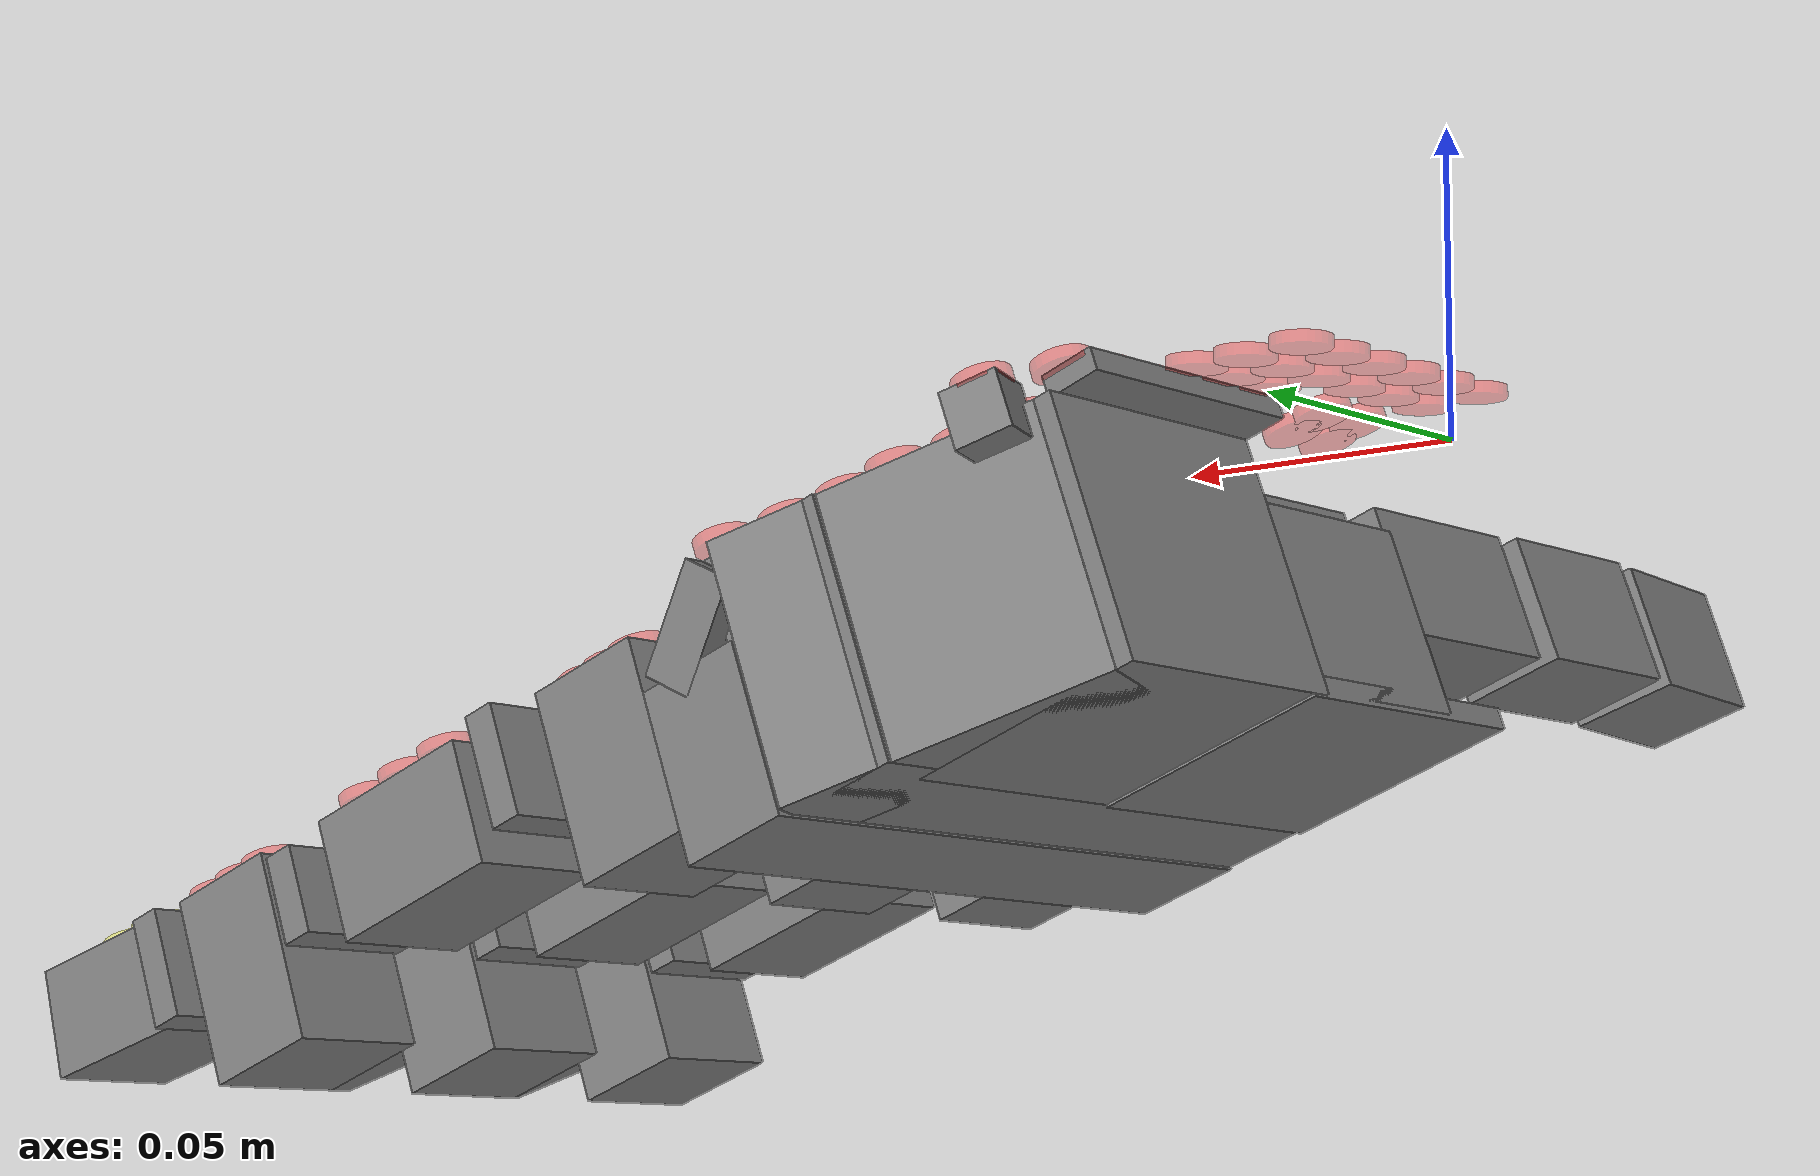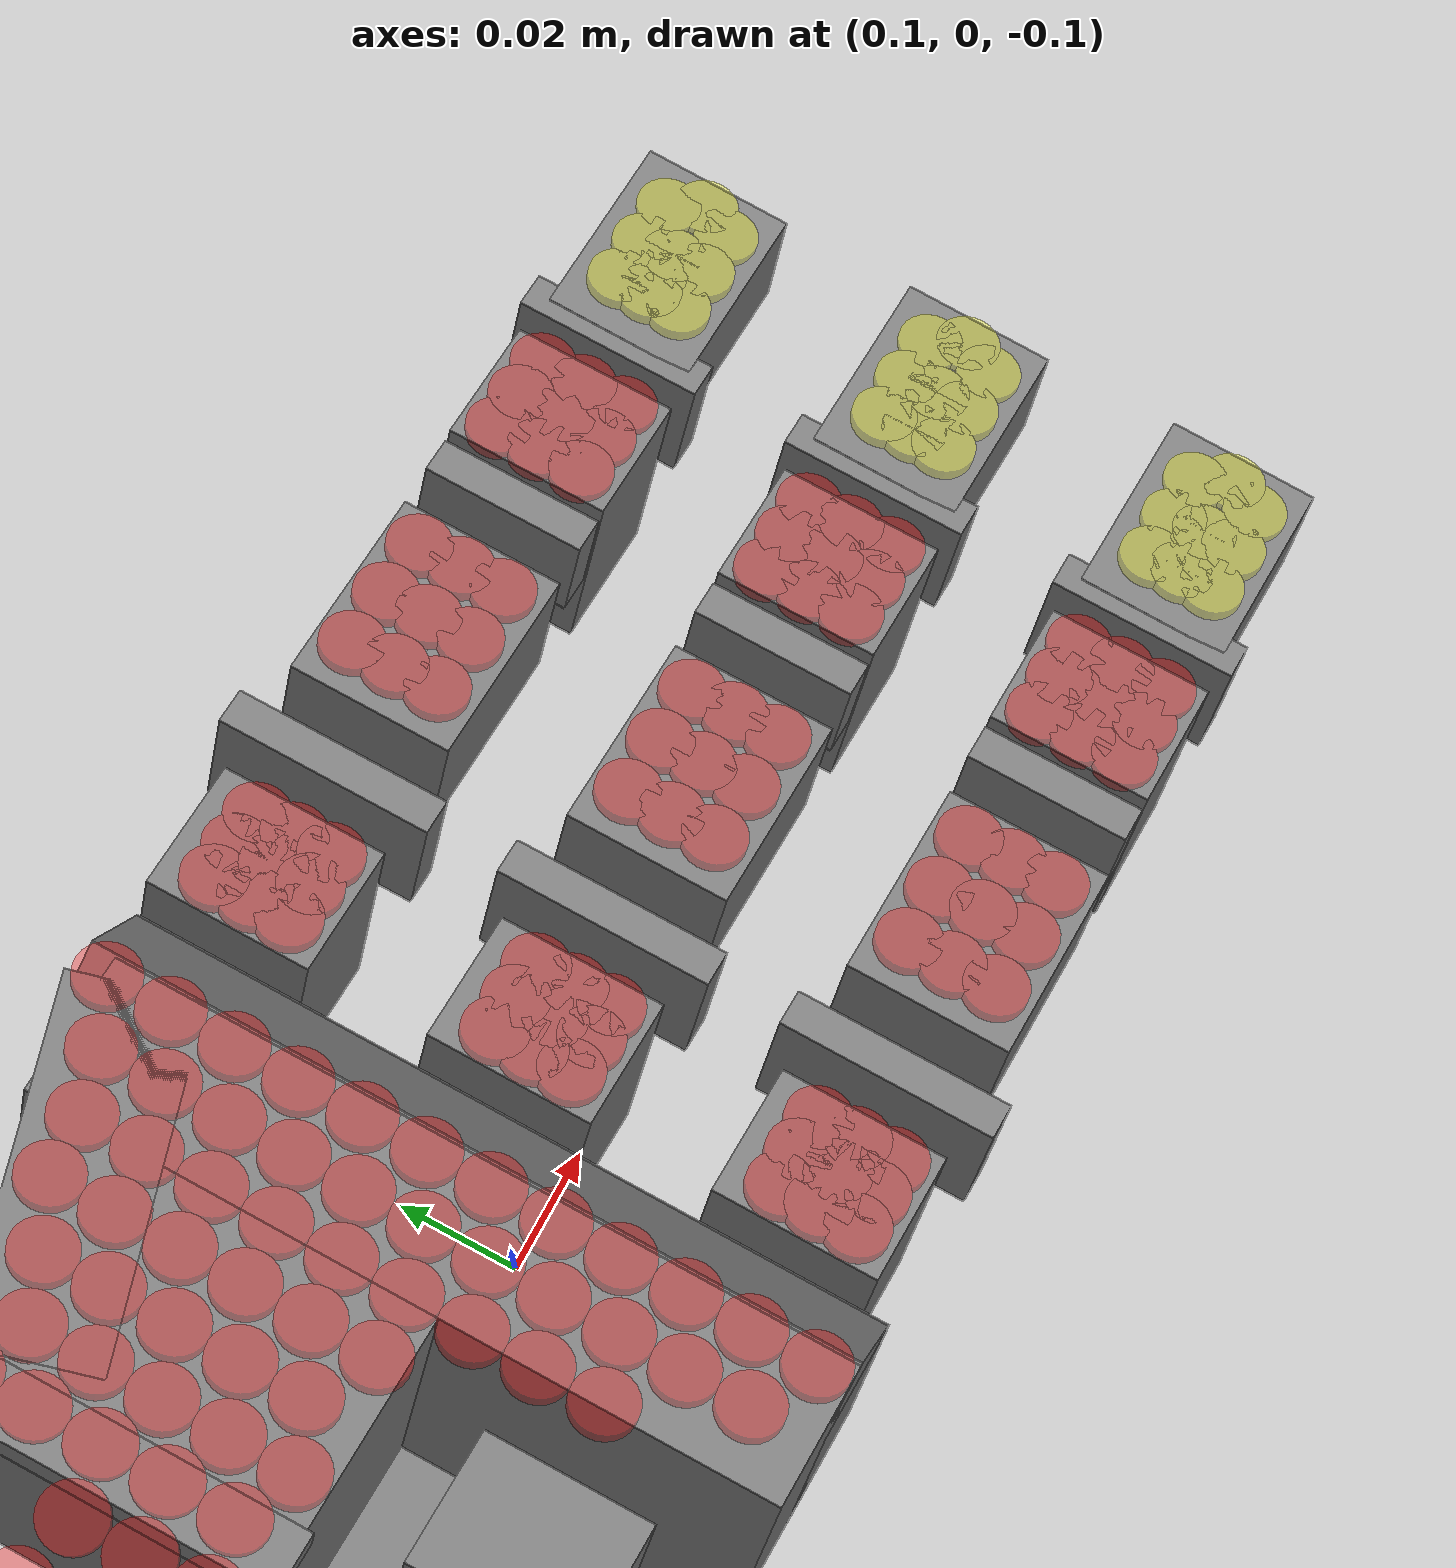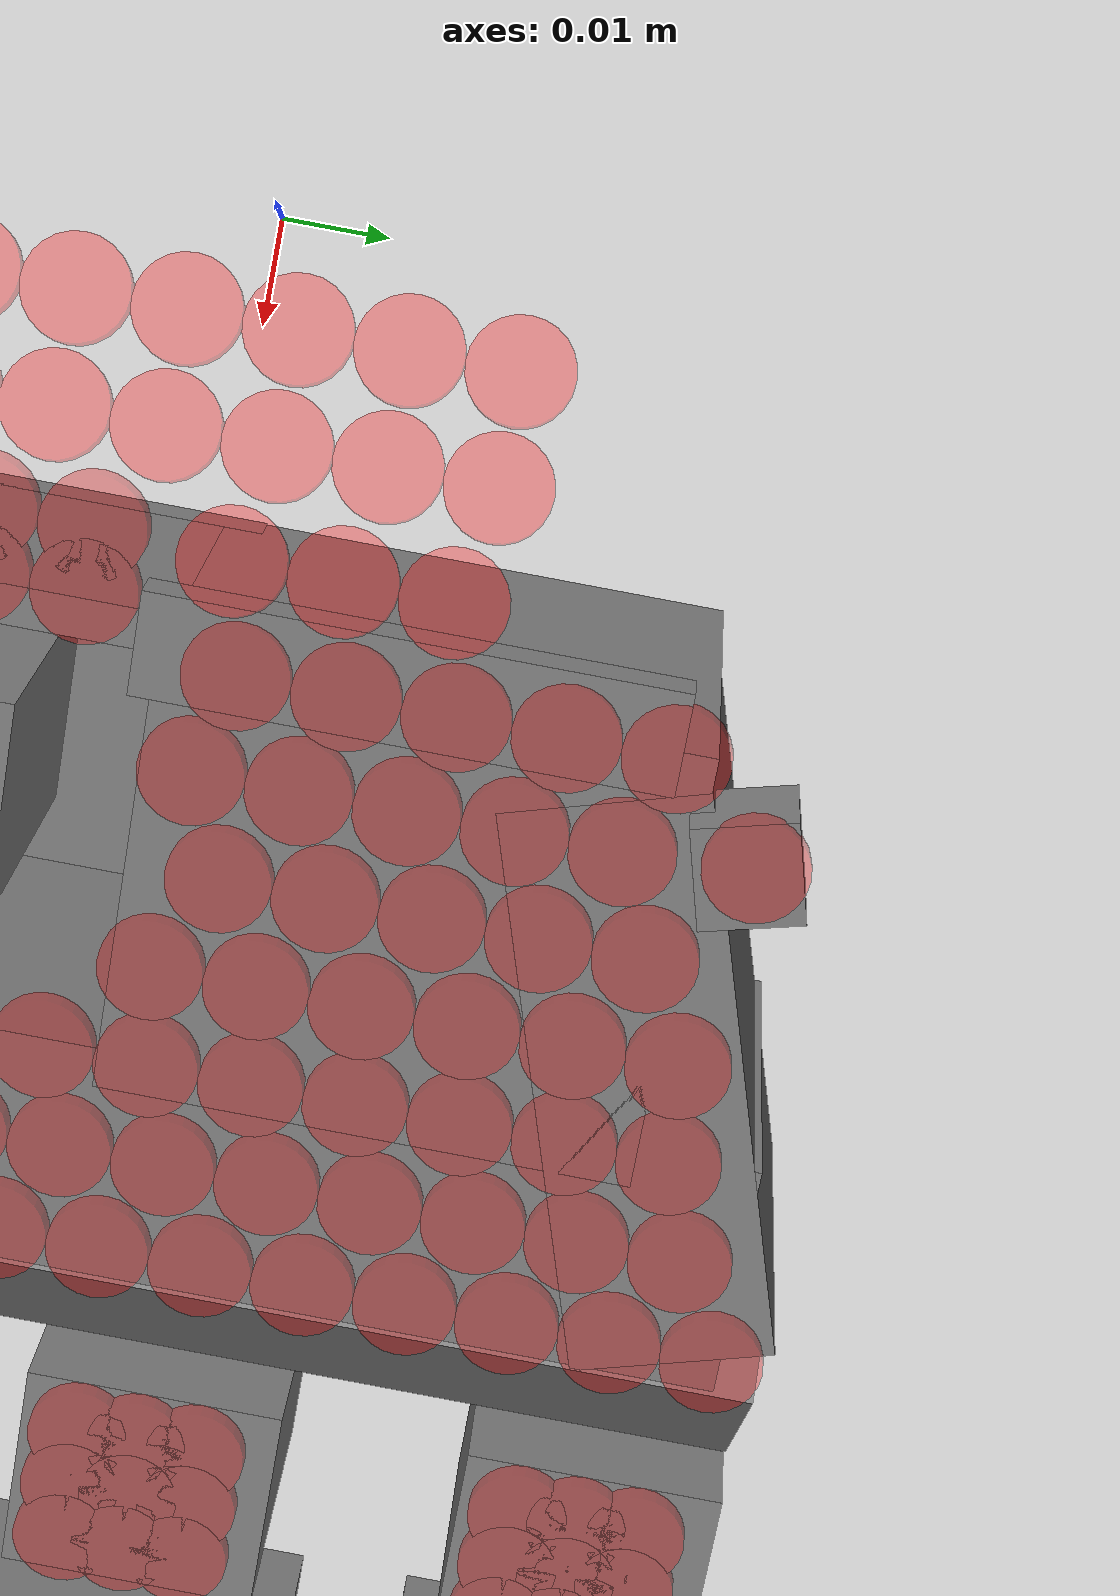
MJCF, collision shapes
<mujoco model="leap_rh">
  <compiler angle="radian" autolimits="true"/>

  <option timestep="0.01" integrator="Euler" iterations="5" ls_iterations="8">
    <flag eulerdamp="disable"/>
  </option>

  <custom>
    <numeric data="30" name="max_contact_points"/>
    <numeric data="12" name="max_geom_pairs"/>
  </custom>

  <asset>
    <material name="black" rgba="0.2 0.2 0.2 1"/>
    <material name="gray" rgba="0.5 0.5 0.5 1"/>
    <mesh name="leap_mount" file="meshes/leap_mount.obj"/>
    <!-- Example path to palm right -->
    <!-- mujoco_playground/external_deps/mujoco_menagerie/leap_hand/assets/palm_right.obj -->
    <!-- original path, incorrect. -->
    <!-- correct path -->
    <mesh name="palm" file="../../../../external_deps/mujoco_menagerie/leap_hand/assets/palm_right.obj"/>
    <mesh name="base" file="../../../../external_deps/mujoco_menagerie/leap_hand/assets/base.obj"/>
    <mesh name="proximal" file="../../../../external_deps/mujoco_menagerie/leap_hand/assets/proximal.obj"/>
    <mesh name="medial" file="../../../../external_deps/mujoco_menagerie/leap_hand/assets/medial.obj"/>
    <mesh name="distal" file="../../../../external_deps/mujoco_menagerie/leap_hand/assets/distal.obj"/>
    <mesh name="tip" file="../../../../external_deps/mujoco_menagerie/leap_hand/assets/tip.obj"/>
    <mesh name="thumb_base" file="../../../../external_deps/mujoco_menagerie/leap_hand/assets/thumb_base.obj"/>
    <mesh name="thumb_proximal" file="../../../../external_deps/mujoco_menagerie/leap_hand/assets/thumb_proximal.obj"/>
    <mesh name="thumb_distal" file="../../../../external_deps/mujoco_menagerie/leap_hand/assets/thumb_distal.obj"/>
    <mesh name="thumb_tip" file="../../../../external_deps/mujoco_menagerie/leap_hand/assets/thumb_tip.obj"/>
  </asset>

  <default>
    <default class="leap_touch">
      <site type="box" size="0.005 0.005 0.005" rgba="0.8 0.8 0.8 0.15" group="4"/>
    </default>
    <default class="leap_rh">
      <geom group="3" friction="0.2" solref="0.02 1.5" solimp="0.9 0.99 0.001"/>
      <default class="visual">
        <geom group="2" type="mesh" contype="0" conaffinity="0" density="0" material="black"/>
      </default>
      <default class="tip">
        <geom size="0.01 0.012 0.016" pos="-0.0012969 -0.0335524 0.0145207" quat="0.703552 0.709596 -0.0292107 -0.0252203" type="box" friction="0.7 0.05 0.0002" rgba=".5 .5 .5 .3"/>
      </default>
      <default class="thumb_tip">
        <geom size="0.01 0.012 0.016" pos="-0.00127744 -0.0455619 -0.0144774" quat="0.708101 0.705072 -0.0294902 -0.024426" type="box" friction="0.7 0.05 0.0002" rgba=".5 .5 .5 .3"/>
      </default>

      <position kp="3.0" inheritrange="1"/>
      <!-- armature = rotor inertia * gear ratio^2 = 1.7 * 1e-8 * 288*288 = 0.00149376 -->
      <!-- max torque = 0.2196 = 600/1000*0.366 -->
      <!-- frictionloss = rough guess, small ish value -->
      <joint axis="0 0 -1" damping="0.2" armature="0.00149376" actuatorfrcrange="-0.2196 0.2196" frictionloss="0.02"/>

      <default class="mcp">
        <joint range="-0.314 2.23"/>
      </default>
      <default class="rot">
        <joint range="-1.047 1.047"/>
      </default>
      <default class="pip">
        <joint range="-0.506 1.885"/>
      </default>
      <default class="dip">
        <joint range="-0.366 2.042"/>
      </default>
      <default class="thumb_cmc">
        <joint range="-0.349 2.094"/>
      </default>
      <default class="thumb_axl">
        <joint range="-0.349 2.094"/>
      </default>
      <default class="thumb_mcp">
        <joint range="-0.47 2.443"/>
      </default>
      <default class="thumb_ipl">
        <joint range="-1.34 1.88"/>
      </default>

    </default>
  </default>

  <contact>
    <!-- filter the palm from all other finger bodies except the tips -->
    <exclude body1="palm" body2="if_bs"/>
    <exclude body1="palm" body2="mf_bs"/>
    <exclude body1="palm" body2="rf_bs"/>
    <exclude body1="palm" body2="th_mp"/>

    <exclude body1="palm" body2="if_px"/>
    <exclude body1="palm" body2="mf_px"/>
    <exclude body1="palm" body2="rf_px"/>
    <exclude body1="palm" body2="th_bs"/>

    <exclude body1="palm" body2="if_md"/>
    <exclude body1="palm" body2="mf_md"/>
    <exclude body1="palm" body2="rf_md"/>
    <exclude body1="palm" body2="th_px"/>

    <!-- filter the mount from all finger bodies except the tips -->
    <exclude body1="leap_mount" body2="if_bs"/>
    <exclude body1="leap_mount" body2="mf_bs"/>
    <exclude body1="leap_mount" body2="rf_bs"/>
    <exclude body1="leap_mount" body2="th_mp"/>

    <exclude body1="leap_mount" body2="if_px"/>
    <exclude body1="leap_mount" body2="mf_px"/>
    <exclude body1="leap_mount" body2="rf_px"/>
    <exclude body1="leap_mount" body2="th_bs"/>

    <exclude body1="leap_mount" body2="if_md"/>
    <exclude body1="leap_mount" body2="mf_md"/>
    <exclude body1="leap_mount" body2="rf_md"/>
    <exclude body1="leap_mount" body2="th_px"/>

    <!-- none of the base fingertip geoms can touch each other -->
    <exclude body1="if_bs" body2="mf_bs"/>
    <exclude body1="if_bs" body2="rf_bs"/>
    <exclude body1="mf_bs" body2="rf_bs"/>

    <exclude body1="th_mp" body2="if_bs"/>
    <exclude body1="th_mp" body2="mf_bs"/>
    <exclude body1="th_mp" body2="rf_bs"/>
  </contact>

  <worldbody>
    <light name="spotlight" mode="targetbodycom" target="palm" pos="3 0 4"/>
    <body name="leap_mount" pos="0 0 0" quat="1 0 0 0" childclass="leap_rh">
      <geom name="leap_mount_visual" pos="0 0 0" quat="1 0 0 0" class="visual" mesh="leap_mount"/>
      <geom name="leap_mount_collision_0" size="0.002 0.025 0.005" pos="0.0405 0.02 0.009"
        quat="0.57346234 0 0.81923192 0" type="box"/>
      <geom name="leap_mount_collision_1" size="0.005 0.005 0.005" pos="0.05 0.053 0.002"
        quat="0.4987168 0.64994038 -0.34910175 0.45495826" type="box"/>
      <site name="grasp_site" pos="0.11 0.0 0.03" group="4"/>
      <body name="palm" pos="0.124 -0.0305 -0.06045" quat="0 1 0 -0.175">
        <inertial pos="-0.049542 -0.042914 -0.010227" quat="0.565586 0.427629 -0.574956 0.408254" mass="0.237"
          diaginertia="0.000407345 0.000304759 0.000180736"/>

        <site name="palm_touch_row0_col0" type="cylinder" pos="-0.04 -0.09 -0.036" size="0.005 0.001" quat="1 0 0 0" rgba="1 0 0 0.33"/>
        <site name="palm_touch_row0_col1" type="cylinder" pos="-0.04 -0.08 -0.036" size="0.005 0.001" quat="1 0 0 0" rgba="1 0 0 0.33"/>
        <site name="palm_touch_row0_col2" type="cylinder" pos="-0.04 -0.07 -0.036" size="0.005 0.001" quat="1 0 0 0" rgba="1 0 0 0.33"/>
        <site name="palm_touch_row0_col3" type="cylinder" pos="-0.04 -0.06 -0.036" size="0.005 0.001" quat="1 0 0 0" rgba="1 0 0 0.33"/>
        <site name="palm_touch_row0_col4" type="cylinder" pos="-0.04 -0.05 -0.036" size="0.005 0.001" quat="1 0 0 0" rgba="1 0 0 0.33"/>
        <site name="palm_touch_row0_col5" type="cylinder" pos="-0.04 -0.04 -0.036" size="0.005 0.001" quat="1 0 0 0" rgba="1 0 0 0.33"/>
        <site name="palm_touch_row0_col6" type="cylinder" pos="-0.04 -0.03 -0.036" size="0.005 0.001" quat="1 0 0 0" rgba="1 0 0 0.33"/>
        <site name="palm_touch_row0_col7" type="cylinder" pos="-0.04 -0.02 -0.036" size="0.005 0.001" quat="1 0 0 0" rgba="1 0 0 0.33"/>
        <site name="palm_touch_row0_col8" type="cylinder" pos="-0.04 -0.01 -0.036" size="0.005 0.001" quat="1 0 0 0" rgba="1 0 0 0.33"/>
        <site name="palm_touch_row0_col9" type="cylinder" pos="-0.04 -0.00 -0.036" size="0.005 0.001" quat="1 0 0 0" rgba="1 0 0 0.33"/>
        <site name="palm_touch_row0_col10" type="cylinder" pos="-0.04 0.01 -0.036" size="0.005 0.001" quat="1 0 0 0" rgba="1 0 0 0.33"/>
        <site name="palm_touch_row0_col11" type="cylinder" pos="-0.04 0.02 -0.036" size="0.005 0.001" quat="1 0 0 0" rgba="1 0 0 0.33"/>

        <site name="palm_touch_row1_col0" type="cylinder" pos="-0.05 -0.085 -0.036" size="0.005 0.001" quat="1 0 0 0" rgba="1 0 0 0.33"/>
        <site name="palm_touch_row1_col1" type="cylinder" pos="-0.05 -0.075 -0.036" size="0.005 0.001" quat="1 0 0 0" rgba="1 0 0 0.33"/>
        <site name="palm_touch_row1_col2" type="cylinder" pos="-0.05 -0.065 -0.036" size="0.005 0.001" quat="1 0 0 0" rgba="1 0 0 0.33"/>
        <site name="palm_touch_row1_col3" type="cylinder" pos="-0.05 -0.055 -0.036" size="0.005 0.001" quat="1 0 0 0" rgba="1 0 0 0.33"/>
        <site name="palm_touch_row1_col4" type="cylinder" pos="-0.05 -0.045 -0.036" size="0.005 0.001" quat="1 0 0 0" rgba="1 0 0 0.33"/>
        <site name="palm_touch_row1_col5" type="cylinder" pos="-0.05 -0.035 -0.036" size="0.005 0.001" quat="1 0 0 0" rgba="1 0 0 0.33"/>
        <site name="palm_touch_row1_col6" type="cylinder" pos="-0.05 -0.025 -0.036" size="0.005 0.001" quat="1 0 0 0" rgba="1 0 0 0.33"/>
        <site name="palm_touch_row1_col7" type="cylinder" pos="-0.05 -0.015 -0.036" size="0.005 0.001" quat="1 0 0 0" rgba="1 0 0 0.33"/>
        <site name="palm_touch_row1_col8" type="cylinder" pos="-0.05 -0.005 -0.036" size="0.005 0.001" quat="1 0 0 0" rgba="1 0 0 0.33"/>
        <site name="palm_touch_row1_col9" type="cylinder" pos="-0.05 0.005 -0.036" size="0.005 0.001" quat="1 0 0 0" rgba="1 0 0 0.33"/>
        <site name="palm_touch_row1_col10" type="cylinder" pos="-0.05 0.015 -0.036" size="0.005 0.001" quat="1 0 0 0" rgba="1 0 0 0.33"/>

        <site name="palm_touch_row2_col0" type="cylinder" pos="-0.06 -0.082 -0.036" size="0.005 0.001" quat="1 0 0 0" rgba="1 0 0 0.33"/>
        <site name="palm_touch_row2_col1" type="cylinder" pos="-0.06 -0.072 -0.036" size="0.005 0.001" quat="1 0 0 0" rgba="1 0 0 0.33"/>
        <site name="palm_touch_row2_col2" type="cylinder" pos="-0.06 -0.062 -0.036" size="0.005 0.001" quat="1 0 0 0" rgba="1 0 0 0.33"/>
        <site name="palm_touch_row2_col3" type="cylinder" pos="-0.06 -0.052 -0.036" size="0.005 0.001" quat="1 0 0 0" rgba="1 0 0 0.33"/>
        <site name="palm_touch_row2_col4" type="cylinder" pos="-0.06 -0.042 -0.036" size="0.005 0.001" quat="1 0 0 0" rgba="1 0 0 0.33"/>
        <site name="palm_touch_row2_col5" type="cylinder" pos="-0.06 -0.032 -0.036" size="0.005 0.001" quat="1 0 0 0" rgba="1 0 0 0.33"/>
        <site name="palm_touch_row2_col6" type="cylinder" pos="-0.06 -0.022 -0.036" size="0.005 0.001" quat="1 0 0 0" rgba="1 0 0 0.33"/>
        <site name="palm_touch_row2_col7" type="cylinder" pos="-0.06 -0.012 -0.036" size="0.005 0.001" quat="1 0 0 0" rgba="1 0 0 0.33"/>
        <site name="palm_touch_row2_col8" type="cylinder" pos="-0.06 -0.002 -0.036" size="0.005 0.001" quat="1 0 0 0" rgba="1 0 0 0.33"/>

        <site name="palm_touch_row3_col0" type="cylinder" pos="-0.07 -0.081 -0.036" size="0.005 0.001" quat="1 0 0 0" rgba="1 0 0 0.33"/>
        <site name="palm_touch_row3_col1" type="cylinder" pos="-0.07 -0.071 -0.036" size="0.005 0.001" quat="1 0 0 0" rgba="1 0 0 0.33"/>
        <site name="palm_touch_row3_col2" type="cylinder" pos="-0.07 -0.061 -0.036" size="0.005 0.001" quat="1 0 0 0" rgba="1 0 0 0.33"/>
        <site name="palm_touch_row3_col3" type="cylinder" pos="-0.07 -0.051 -0.036" size="0.005 0.001" quat="1 0 0 0" rgba="1 0 0 0.33"/>
        <site name="palm_touch_row3_col4" type="cylinder" pos="-0.07 -0.041 -0.036" size="0.005 0.001" quat="1 0 0 0" rgba="1 0 0 0.33"/>
        <site name="palm_touch_row3_col5" type="cylinder" pos="-0.07 -0.031 -0.036" size="0.005 0.001" quat="1 0 0 0" rgba="1 0 0 0.33"/>

        <site name="palm_touch_row4_col0" type="cylinder" pos="-0.08 -0.076 -0.036" size="0.005 0.001" quat="1 0 0 0" rgba="1 0 0 0.33"/>
        <site name="palm_touch_row4_col1" type="cylinder" pos="-0.08 -0.066 -0.036" size="0.005 0.001" quat="1 0 0 0" rgba="1 0 0 0.33"/>
        <site name="palm_touch_row4_col2" type="cylinder" pos="-0.08 -0.056 -0.036" size="0.005 0.001" quat="1 0 0 0" rgba="1 0 0 0.33"/>
        <site name="palm_touch_row4_col3" type="cylinder" pos="-0.08 -0.046 -0.036" size="0.005 0.001" quat="1 0 0 0" rgba="1 0 0 0.33"/>
        <site name="palm_touch_row4_col4" type="cylinder" pos="-0.08 -0.036 -0.036" size="0.005 0.001" quat="1 0 0 0" rgba="1 0 0 0.33"/>

        <site name="palm_touch_row5_col0" type="cylinder" pos="-0.092 -0.084 -0.039" size="0.005 0.001" quat="1 0 0 0" rgba="1 0 0 0.33"/>
        <site name="palm_touch_row5_col1" type="cylinder" pos="-0.09 -0.072 -0.036" size="0.005 0.001" quat="1 0 0 0" rgba="1 0 0 0.33"/>
        <site name="palm_touch_row5_col2" type="cylinder" pos="-0.09 -0.062 -0.036" size="0.005 0.001" quat="1 0 0 0" rgba="1 0 0 0.33"/>
        <site name="palm_touch_row5_col3" type="cylinder" pos="-0.09 -0.052 -0.036" size="0.005 0.001" quat="1 0 0 0" rgba="1 0 0 0.33"/>
        <site name="palm_touch_row5_col4" type="cylinder" pos="-0.09 -0.042 -0.036" size="0.005 0.001" quat="1 0 0 0" rgba="1 0 0 0.33"/>
        <site name="palm_touch_row5_col5" type="cylinder" pos="-0.09 -0.032 -0.036" size="0.005 0.001" quat="1 0 0 0" rgba="1 0 0 0.33"/>

        <site name="palm_touch_row6_col0" type="cylinder" pos="-0.101 -0.075 -0.039" size="0.005 0.001" quat="1 0 0 0" rgba="1 0 0 0.33"/>
        <site name="palm_touch_row6_col1" type="cylinder" pos="-0.101 -0.065 -0.039" size="0.005 0.001" quat="1 0 0 0" rgba="1 0 0 0.33"/>
        <site name="palm_touch_row6_col2" type="cylinder" pos="-0.101 -0.055 -0.039" size="0.005 0.001" quat="1 0 0 0" rgba="1 0 0 0.33"/>
        <site name="palm_touch_row6_col3" type="cylinder" pos="-0.101 -0.045 -0.039" size="0.005 0.001" quat="1 0 0 0" rgba="1 0 0 0.33"/>
        <site name="palm_touch_row6_col4" type="cylinder" pos="-0.101 -0.035 -0.039" size="0.005 0.001" quat="1 0 0 0" rgba="1 0 0 0.33"/>
        <site name="palm_touch_row6_col5" type="cylinder" pos="-0.105 -0.02 -0.035" size="0.005 0.001" quat="1 0 0 0" rgba="1 0 0 0.33"/>
        <site name="palm_touch_row6_col6" type="cylinder" pos="-0.105 -0.01 -0.035" size="0.005 0.001" quat="1 0 0 0" rgba="1 0 0 0.33"/>

        <site name="palm_touch_row7_col0" type="cylinder" pos="-0.111 -0.053 -0.038" size="0.005 0.001" quat="0.9848078 0 0.1736482 0" rgba="1 0 0 0.33"/>
        <site name="palm_touch_row7_col1" type="cylinder" pos="-0.111 -0.043 -0.038" size="0.005 0.001" quat="0.9848078 0 0.1736482 0" rgba="1 0 0 0.33"/>
        <site name="palm_touch_row7_col2" type="cylinder" pos="-0.111 -0.033 -0.038" size="0.005 0.001" quat="0.9848078 0 0.1736482 0" rgba="1 0 0 0.33"/>
        <site name="palm_touch_row7_col3" type="cylinder" pos="-0.111 -0.02 -0.035" size="0.005 0.001" quat="1 0 0 0" rgba="1 0 0 0.33"/>
        <site name="palm_touch_row7_col4" type="cylinder" pos="-0.111 -0.01 -0.035" size="0.005 0.001" quat="1 0 0 0" rgba="1 0 0 0.33"/>

        <site name="palm_touch_row8_col0" type="cylinder" pos="-0.121 -0.055 -0.034" size="0.005 0.001" quat="0.9848078 0 0.1736482 0" rgba="1 0 0 0.33"/>
        <site name="palm_touch_row8_col1" type="cylinder" pos="-0.121 -0.045 -0.034" size="0.005 0.001" quat="0.9848078 0 0.1736482 0" rgba="1 0 0 0.33"/>
        <site name="palm_touch_row8_col2" type="cylinder" pos="-0.121 -0.035 -0.034" size="0.005 0.001" quat="0.9848078 0 0.1736482 0" rgba="1 0 0 0.33"/>
        <site name="palm_touch_row8_col3" type="cylinder" pos="-0.121 -0.025 -0.034" size="0.005 0.001" quat="0.9848078 0 0.1736482 0" rgba="1 0 0 0.33"/>
        <site name="palm_touch_row8_col4" type="cylinder" pos="-0.121 -0.015 -0.034" size="0.005 0.001" quat="0.9848078 0 0.1736482 0" rgba="1 0 0 0.33"/>
        <site name="palm_touch_row8_col5" type="cylinder" pos="-0.121 -0.005 -0.034" size="0.005 0.001" quat="0.9848078 0 0.1736482 0" rgba="1 0 0 0.33"/>

        <site name="palm_touch_row9_col0" type="cylinder" pos="-0.131 -0.055 -0.031" size="0.005 0.001" quat="0.9848078 0 0.1736482 0" rgba="1 0 0 0.33"/>
        <site name="palm_touch_row9_col1" type="cylinder" pos="-0.131 -0.045 -0.031" size="0.005 0.001" quat="0.9848078 0 0.1736482 0" rgba="1 0 0 0.33"/>
        <site name="palm_touch_row9_col2" type="cylinder" pos="-0.131 -0.035 -0.031" size="0.005 0.001" quat="0.9848078 0 0.1736482 0" rgba="1 0 0 0.33"/>
        <site name="palm_touch_row9_col3" type="cylinder" pos="-0.131 -0.025 -0.031" size="0.005 0.001" quat="0.9848078 0 0.1736482 0" rgba="1 0 0 0.33"/>
        <site name="palm_touch_row9_col4" type="cylinder" pos="-0.131 -0.015 -0.031" size="0.005 0.001" quat="0.9848078 0 0.1736482 0" rgba="1 0 0 0.33"/>
        <site name="palm_touch_row9_col5" type="cylinder" pos="-0.131 -0.005 -0.031" size="0.005 0.001" quat="0.9848078 0 0.1736482 0" rgba="1 0 0 0.33"/>

        <geom name="palm_visual" pos="-0.02 0.02575 -0.0347" quat="1 0 0 0" class="visual" mesh="palm"/>

        <site name="palm_touch_if" type="cylinder" size="0.005 0.001" pos="-0.009 0.009 -0.029"  rgba="1 0 0 0.33"/>
        <site name="palm_touch_if_down" type="cylinder" size="0.005 0.001" pos="-0.015 0.009 -0.029"  rgba="1 0 0 0.33"/>
        <site name="palm_touch_if_up" type="cylinder" size="0.005 0.001" pos="-0.003 0.009 -0.029"  rgba="1 0 0 0.33"/>
        <site name="palm_touch_if_left" type="cylinder" size="0.005 0.001" pos="-0.009 0.003 -0.029"  rgba="1 0 0 0.33"/>
        <site name="palm_touch_if_right" type="cylinder" size="0.005 0.001" pos="-0.009 0.015 -0.029"  rgba="1 0 0 0.33"/>
        <site name="palm_touch_if_left_up" type="cylinder" size="0.005 0.001" pos="-0.003 0.003 -0.029"  rgba="1 0 0 0.33"/>
        <site name="palm_touch_if_right_up" type="cylinder" size="0.005 0.001" pos="-0.003 0.015 -0.029"  rgba="1 0 0 0.33"/>
        <site name="palm_touch_if_left_down" type="cylinder" size="0.005 0.001" pos="-0.015 0.003 -0.029"  rgba="1 0 0 0.33"/>
        <site name="palm_touch_if_right_down" type="cylinder" size="0.005 0.001" pos="-0.015 0.015 -0.029"  rgba="1 0 0 0.33"/>

        <geom name="palm_collision_1" size="0.011 0.013 0.017" pos="-0.009 0.008 -0.011" type="box"/>

        <site name="palm_touch_mf" type="cylinder" size="0.005 0.001" pos="-0.009 -0.036 -0.029" rgba="1 0 0 0.33"/>
        <site name="palm_touch_mf_down" type="cylinder" size="0.005 0.001" pos="-0.015 -0.036 -0.029" rgba="1 0 0 0.33"/>
        <site name="palm_touch_mf_up" type="cylinder" size="0.005 0.001" pos="-0.003 -0.036 -0.029" rgba="1 0 0 0.33"/>
        <site name="palm_touch_mf_left" type="cylinder" size="0.005 0.001" pos="-0.009 -0.030 -0.029" rgba="1 0 0 0.33"/>
        <site name="palm_touch_mf_right" type="cylinder" size="0.005 0.001" pos="-0.009 -0.042 -0.029" rgba="1 0 0 0.33"/>
        <site name="palm_touch_mf_left_up" type="cylinder" size="0.005 0.001" pos="-0.003 -0.030 -0.029" rgba="1 0 0 0.33"/>
        <site name="palm_touch_mf_right_up" type="cylinder" size="0.005 0.001" pos="-0.003 -0.042 -0.029" rgba="1 0 0 0.33"/>
        <site name="palm_touch_mf_left_down" type="cylinder" size="0.005 0.001" pos="-0.015 -0.030 -0.029" rgba="1 0 0 0.33"/>
        <site name="palm_touch_mf_right_down" type="cylinder" size="0.005 0.001" pos="-0.015 -0.042 -0.029" rgba="1 0 0 0.33"/>

        <geom name="palm_collision_2" size="0.011 0.013 0.017" pos="-0.009 -0.037 -0.011" type="box"/>

        <site name="palm_touch_rf" type="cylinder" size="0.005 0.001" pos="-0.009 -0.081 -0.029" rgba="1 0 0 0.33"/>
        <site name="palm_touch_rf_down" type="cylinder" size="0.005 0.001" pos="-0.015 -0.081 -0.029" rgba="1 0 0 0.33"/>
        <site name="palm_touch_rf_up" type="cylinder" size="0.005 0.001" pos="-0.003 -0.081 -0.029" rgba="1 0 0 0.33"/>
        <site name="palm_touch_rf_left" type="cylinder" size="0.005 0.001" pos="-0.009 -0.075 -0.029" rgba="1 0 0 0.33"/>
        <site name="palm_touch_rf_right" type="cylinder" size="0.005 0.001" pos="-0.009 -0.087 -0.029" rgba="1 0 0 0.33"/>
        <site name="palm_touch_rf_left_up" type="cylinder" size="0.005 0.001" pos="-0.003 -0.075 -0.029" rgba="1 0 0 0.33"/>
        <site name="palm_touch_rf_right_up" type="cylinder" size="0.005 0.001" pos="-0.003 -0.087 -0.029" rgba="1 0 0 0.33"/>
        <site name="palm_touch_rf_left_down" type="cylinder" size="0.005 0.001" pos="-0.015 -0.075 -0.029" rgba="1 0 0 0.33"/>
        <site name="palm_touch_rf_right_down" type="cylinder" size="0.005 0.001" pos="-0.015 -0.087 -0.029" rgba="1 0 0 0.33"/>

        <geom name="palm_collision_3" size="0.011 0.013 0.017" pos="-0.009 -0.082 -0.011" type="box"/>
        <geom name="palm_collision_4" size="0.029 0.01 0.023" pos="-0.066 -0.078 -0.0115" quat="0.989016 0 0 -0.147806" type="box"/>
        <geom name="palm_collision_5" size="0.01 0.06 0.015" pos="-0.03 -0.035 -0.003" type="box"/>
        <geom name="palm_collision_6" size="0.005 0.06 0.01" pos="-0.032 -0.035 -0.024" quat="0.923956 0 0.382499 0" type="box"/>
        <geom name="palm_collision_7" size="0.012 0.058 0.023" pos="-0.048 -0.033 -0.0115" type="box"/>
        <geom name="palm_collision_8" size="0.022 0.026 0.023" pos="-0.078 -0.053 -0.0115" type="box"/>
        <geom name="palm_collision_9" size="0.002 0.018 0.017" pos="-0.098 -0.009 -0.006" type="box"/>
        <geom name="palm_collision_10" size="0.022 0.028 0.002" pos="-0.078 -0.003 0.01" type="box"/>
        <body name="if_bs" pos="-0.007 0.023 -0.0187" quat="0.5 0.5 0.5 -0.5">
          <inertial pos="-0.022516 0.033882 0.016359" quat="0.388092 0.677951 -0.247713 0.573067" mass="0.044"
            diaginertia="1.74972e-05 1.61504e-05 7.21342e-06"/>
          <joint name="if_mcp" class="mcp"/>
          <geom name="if_bs_visual" pos="0.0084 0.0077 0.01465" quat="1 0 0 0" class="visual" mesh="base"/>
          <geom name="if_bs_collision_1" size="0.01 0.003 0.017" pos="0 0.018 0.0147" type="box"/>
          <body name="if_px" pos="-0.0122 0.0381 0.0145" quat="0.500003 -0.5 -0.499997 0.5">
            <inertial pos="0.0075 -0.0002 -0.011" quat="0 0.707107 0 0.707107" mass="0.032"
              diaginertia="4.8853e-06 4.3733e-06 3.0933e-06"/>
            <joint name="if_rot" class="rot"/>
            <geom name="if_px_visual" pos="0.0096 0.0002 0.0007" quat="0.500003 -0.5 -0.5 -0.499997" class="visual"
              mesh="proximal"/>
            <geom name="if_px_collision" size="0.017 0.013 0.011" pos="0.0075 -0.0002 -0.011" type="box"/>

            <site name="if_px_touch" type="cylinder" size="0.005 0.001" pos="0.0075 -0.0002 -0.024" rgba="1 0 0 0.33"/>
            <site name="if_px_touch_left" type="cylinder" size="0.005 0.001" pos="0.0075 0.0068 -0.024" rgba="1 0 0 0.33"/>
            <site name="if_px_touch_right" type="cylinder" size="0.005 0.001" pos="0.0075 -0.0072 -0.024" rgba="1 0 0 0.33"/>
            <site name="if_px_touch_up" type="cylinder" size="0.005 0.001" pos="0.0175 -0.0002 -0.024" rgba="1 0 0 0.33"/>
            <site name="if_px_touch_down" type="cylinder" size="0.005 0.001" pos="-0.0025 -0.0002 -0.024" rgba="1 0 0 0.33"/>
            <site name="if_px_touch_left_down" type="cylinder" size="0.005 0.001" pos="-0.0025 0.0068 -0.024" rgba="1 0 0 0.33"/>
            <site name="if_px_touch_left_up" type="cylinder" size="0.005 0.001" pos="0.0175 0.0068 -0.024" rgba="1 0 0 0.33"/>
            <site name="if_px_touch_right_down" type="cylinder" size="0.005 0.001" pos="-0.0025 -0.0072 -0.024" rgba="1 0 0 0.33"/>
            <site name="if_px_touch_right_up" type="cylinder" size="0.005 0.001" pos="0.0175 -0.0072 -0.024" rgba="1 0 0 0.33"/>

            <body name="if_md" pos="0.015 0.0143 -0.013" quat="0.500003 0.5 -0.5 0.499997">
              <inertial pos="0.0054215 -0.029148 0.015" quat="0.687228 0.687228 0.166487 0.166487" mass="0.037"
                diaginertia="8.28004e-06 8.1598e-06 5.39516e-06"/>
              <joint name="if_pip" class="pip"/>
              <geom name="if_md_visual" pos="0.0211 -0.0084 0.0097" quat="2.67949e-08 -1 0 0" class="visual"
                mesh="medial"/>
              <geom name="if_md_collision_1" size="0.008 0.003 0.013" pos="0 -0.02 0.015" type="box"/>
              <geom name="if_md_collision_5" size="0.017 0.011 0.013" pos="0.0075 -0.035 0.015" type="box"/>

              <site name="if_md_touch" type="cylinder" pos="-0.01 -0.035 0.015" size="0.005 0.001" quat="0.7071068 0 0.7071068 0" rgba="1 0 0 0.33"/>
              <site name="if_md_touch_left" type="cylinder" pos="-0.01 -0.035 0.008" size="0.005 0.001" quat="0.7071068 0 0.7071068 0" rgba="1 0 0 0.33"/>
              <site name="if_md_touch_right" type="cylinder" pos="-0.01 -0.035 0.022" size="0.005 0.001" quat="0.7071068 0 0.7071068 0" rgba="1 0 0 0.33"/>
              <site name="if_md_touch_up" type="cylinder" pos="-0.01 -0.042 0.015" size="0.005 0.001" quat="0.7071068 0 0.7071068 0" rgba="1 0 0 0.33"/>
              <site name="if_md_touch_down" type="cylinder" pos="-0.01 -0.028 0.015" size="0.005 0.001" quat="0.7071068 0 0.7071068 0" rgba="1 0 0 0.33"/>
              <site name="if_md_touch_left_down" type="cylinder" pos="-0.01 -0.028 0.008" size="0.005 0.001" quat="0.7071068 0 0.7071068 0" rgba="1 0 0 0.33"/>
              <site name="if_md_touch_left_up" type="cylinder" pos="-0.01 -0.042 0.008" size="0.005 0.001" quat="0.7071068 0 0.7071068 0" rgba="1 0 0 0.33"/>
              <site name="if_md_touch_right_down" type="cylinder" pos="-0.01 -0.028 0.022" size="0.005 0.001" quat="0.7071068 0 0.7071068 0" rgba="1 0 0 0.33"/>
              <site name="if_md_touch_right_up" type="cylinder" pos="-0.01 -0.042 0.022" size="0.005 0.001" quat="0.7071068 0 0.7071068 0" rgba="1 0 0 0.33"/>

              <body name="if_ds" pos="0 -0.0361 0.0002">
                <inertial pos="-0.0008794 -0.027019 0.014594" quat="0.702905 0.710643 -0.0212937 -0.0214203"
                  mass="0.016" diaginertia="3.71863e-06 3.02396e-06 1.6518e-06"/>
                <joint name="if_dip" class="dip"/>
                <geom name="if_ds_visual" pos="0.0132 -0.0061 0.0144" quat="2.67949e-08 1 0 0" class="visual"
                  mesh="distal"/>
                <geom name="if_ds_collision_1" size="0.01 0.003 0.015" pos="0 -0.017 0.015" type="box"/>
                <geom name="if_tip" class="tip"/>
                <geom type="mesh" mesh="tip" class="visual" material="gray"/>
                <site name="if_tip" pos="0 -0.05 0.015" group="4" />

                <site name="if_tip_touch" type="cylinder" pos="-0.012 -0.033 0.014" size="0.005 0.001" quat="0.7071068 0 0.7071068 0" rgba="1 1 0 0.33"/>
                <site name="if_tip_touch_left" type="cylinder" pos="-0.012 -0.033 0.009" size="0.005 0.001" quat="0.7071068 0 0.7071068 0" rgba="1 1 0 0.33"/>
                <site name="if_tip_touch_right" type="cylinder" pos="-0.012 -0.033 0.019" size="0.005 0.001" quat="0.7071068 0 0.7071068 0" rgba="1 1 0 0.33"/>
                <site name="if_tip_touch_up" type="cylinder" pos="-0.012 -0.044 0.014" size="0.005 0.001" quat="0.7071068 0 0.7071068 0" rgba="1 1 0 0.33"/>
                <site name="if_tip_touch_down" type="cylinder" pos="-0.012 -0.025 0.014" size="0.005 0.001" quat="0.7071068 0 0.7071068 0" rgba="1 1 0 0.33"/>
                <site name="if_tip_touch_left_down" type="cylinder" pos="-0.012 -0.025 0.009" size="0.005 0.001" quat="0.7071068 0 0.7071068 0" rgba="1 1 0 0.33"/>
                <site name="if_tip_touch_right_down" type="cylinder" pos="-0.012 -0.025 0.019" size="0.005 0.001" quat="0.7071068 0 0.7071068 0" rgba="1 1 0 0.33"/>
                <site name="if_tip_touch_left_up" type="cylinder" pos="-0.012 -0.041 0.009" size="0.005 0.001" quat="0.7071068 0 0.7071068 0" rgba="1 1 0 0.33"/>
                <site name="if_tip_touch_right_up" type="cylinder" pos="-0.012 -0.041 0.019" size="0.005 0.001" quat="0.7071068 0 0.7071068 0" rgba="1 1 0 0.33"/>

              </body>
            </body>
          </body>
        </body>
        <body name="mf_bs" pos="-0.0071 -0.0224 -0.0187" quat="0.500003 0.5 0.5 -0.499997">
          <inertial pos="-0.022516 0.033882 0.016359" quat="0.388092 0.677951 -0.247713 0.573067" mass="0.044"
            diaginertia="1.74972e-05 1.61504e-05 7.21342e-06"/>
          <joint name="mf_mcp" class="mcp"/>
          <geom name="mf_bs_visual" pos="0.0084 0.0077 0.01465" quat="1 0 0 0" class="visual" mesh="base"/>
          <geom name="mf_bs_collision_1" size="0.01 0.003 0.017" pos="0 0.018 0.0147" type="box"/>
          <body name="mf_px" pos="-0.0122 0.0381 0.0145" quat="0.500003 -0.5 -0.499997 0.5">
            <inertial pos="0.0075 -0.0002 -0.011" quat="0 0.707107 0 0.707107" mass="0.032"
              diaginertia="4.8853e-06 4.3733e-06 3.0933e-06"/>
            <joint name="mf_rot" class="rot"/>
            <geom name="mf_px_visual" pos="0.0096 0.0003 0.0007" quat="0.500003 -0.5 -0.5 -0.499997" class="visual"
              mesh="proximal"/>
            <geom name="mf_px_collision" size="0.017 0.013 0.011" pos="0.0075 -0.0002 -0.011" type="box"/>
            <site name="mf_px_touch" type="cylinder" size="0.005 0.001" pos="0.0075 -0.0002 -0.024" rgba="1 0 0 0.33"/>
            <site name="mf_px_touch_left" type="cylinder" size="0.005 0.001" pos="0.0075 0.0068 -0.024" rgba="1 0 0 0.33"/>
            <site name="mf_px_touch_right" type="cylinder" size="0.005 0.001" pos="0.0075 -0.0072 -0.024" rgba="1 0 0 0.33"/>
            <site name="mf_px_touch_up" type="cylinder" size="0.005 0.001" pos="0.0175 -0.0002 -0.024" rgba="1 0 0 0.33"/>
            <site name="mf_px_touch_down" type="cylinder" size="0.005 0.001" pos="-0.0025 -0.0002 -0.024" rgba="1 0 0 0.33"/>
            <site name="mf_px_touch_left_down" type="cylinder" size="0.005 0.001" pos="-0.0025 0.0068 -0.024" rgba="1 0 0 0.33"/>
            <site name="mf_px_touch_left_up" type="cylinder" size="0.005 0.001" pos="0.0175 0.0068 -0.024" rgba="1 0 0 0.33"/>
            <site name="mf_px_touch_right_down" type="cylinder" size="0.005 0.001" pos="-0.0025 -0.0072 -0.024" rgba="1 0 0 0.33"/>
            <site name="mf_px_touch_right_up" type="cylinder" size="0.005 0.001" pos="0.0175 -0.0072 -0.024" rgba="1 0 0 0.33"/>
            <body name="mf_md" pos="0.015 0.0143 -0.013" quat="0.500003 0.5 -0.5 0.499997">
              <inertial pos="0.0054215 -0.029148 0.015" quat="0.687228 0.687228 0.166487 0.166487" mass="0.037"
                diaginertia="8.28004e-06 8.1598e-06 5.39516e-06"/>
              <joint name="mf_pip" class="pip"/>
              <geom name="mf_md_visual" pos="0.0211 -0.0084 0.0097" quat="1.32679e-06 -1 0 0" class="visual"
                mesh="medial"/>
              <geom name="mf_md_collision_1" size="0.008 0.003 0.013" pos="0 -0.02 0.015" type="box"/>
              <geom name="mf_md_collision_5" size="0.017 0.011 0.013" pos="0.0075 -0.035 0.015" type="box"/>
              <site name="mf_md_touch" type="cylinder" pos="-0.01 -0.035 0.015" size="0.005 0.001" quat="0.7071068 0 0.7071068 0" rgba="1 0 0 0.33"/>
              <site name="mf_md_touch_left" type="cylinder" pos="-0.01 -0.035 0.008" size="0.005 0.001" quat="0.7071068 0 0.7071068 0" rgba="1 0 0 0.33"/>
              <site name="mf_md_touch_right" type="cylinder" pos="-0.01 -0.035 0.022" size="0.005 0.001" quat="0.7071068 0 0.7071068 0" rgba="1 0 0 0.33"/>
              <site name="mf_md_touch_up" type="cylinder" pos="-0.01 -0.042 0.015" size="0.005 0.001" quat="0.7071068 0 0.7071068 0" rgba="1 0 0 0.33"/>
              <site name="mf_md_touch_down" type="cylinder" pos="-0.01 -0.028 0.015" size="0.005 0.001" quat="0.7071068 0 0.7071068 0" rgba="1 0 0 0.33"/>
              <site name="mf_md_touch_left_down" type="cylinder" pos="-0.01 -0.028 0.008" size="0.005 0.001" quat="0.7071068 0 0.7071068 0" rgba="1 0 0 0.33"/>
              <site name="mf_md_touch_left_up" type="cylinder" pos="-0.01 -0.042 0.008" size="0.005 0.001" quat="0.7071068 0 0.7071068 0" rgba="1 0 0 0.33"/>
              <site name="mf_md_touch_right_down" type="cylinder" pos="-0.01 -0.028 0.022" size="0.005 0.001" quat="0.7071068 0 0.7071068 0" rgba="1 0 0 0.33"/>
              <site name="mf_md_touch_right_up" type="cylinder" pos="-0.01 -0.042 0.022" size="0.005 0.001" quat="0.7071068 0 0.7071068 0" rgba="1 0 0 0.33"/>
              <body name="mf_ds" pos="0 -0.0361 0.0002">
                <inertial pos="-0.0008794 -0.027019 0.014594" quat="0.702905 0.710643 -0.0212937 -0.0214203"
                  mass="0.016" diaginertia="3.71863e-06 3.02396e-06 1.6518e-06"/>
                <joint name="mf_dip" class="dip"/>
                <geom name="mf_ds_visual" pos="0.0132 -0.0061 0.0145" quat="1.32679e-06 1 0 0" class="visual"
                  mesh="distal"/>
                <geom name="mf_ds_collision_1" size="0.01 0.003 0.015" pos="0 -0.017 0.015" type="box"/>
                <geom name="mf_tip" class="tip"/>
                <geom type="mesh" mesh="tip" class="visual" material="gray"/>
                <site name="mf_tip" pos="0 -0.05 0.015" group="4"/>
                <site name="mf_tip_touch" type="cylinder" pos="-0.012 -0.033 0.014" size="0.005 0.001" quat="0.7071068 0 0.7071068 0" rgba="1 1 0 0.33"/>
                <site name="mf_tip_touch_left" type="cylinder" pos="-0.012 -0.033 0.009" size="0.005 0.001" quat="0.7071068 0 0.7071068 0" rgba="1 1 0 0.33"/>
                <site name="mf_tip_touch_right" type="cylinder" pos="-0.012 -0.033 0.019" size="0.005 0.001" quat="0.7071068 0 0.7071068 0" rgba="1 1 0 0.33"/>
                <site name="mf_tip_touch_up" type="cylinder" pos="-0.012 -0.044 0.014" size="0.005 0.001" quat="0.7071068 0 0.7071068 0" rgba="1 1 0 0.33"/>
                <site name="mf_tip_touch_down" type="cylinder" pos="-0.012 -0.025 0.014" size="0.005 0.001" quat="0.7071068 0 0.7071068 0" rgba="1 1 0 0.33"/>
                <site name="mf_tip_touch_left_down" type="cylinder" pos="-0.012 -0.025 0.009" size="0.005 0.001" quat="0.7071068 0 0.7071068 0" rgba="1 1 0 0.33"/>
                <site name="mf_tip_touch_right_down" type="cylinder" pos="-0.012 -0.025 0.019" size="0.005 0.001" quat="0.7071068 0 0.7071068 0" rgba="1 1 0 0.33"/>
                <site name="mf_tip_touch_left_up" type="cylinder" pos="-0.012 -0.041 0.009" size="0.005 0.001" quat="0.7071068 0 0.7071068 0" rgba="1 1 0 0.33"/>
                <site name="mf_tip_touch_right_up" type="cylinder" pos="-0.012 -0.041 0.019" size="0.005 0.001" quat="0.7071068 0 0.7071068 0" rgba="1 1 0 0.33"/>
              </body>
            </body>
          </body>
        </body>
        <body name="rf_bs" pos="-0.00709 -0.0678 -0.0187" quat="0.500003 0.5 0.5 -0.499997">
          <inertial pos="-0.022516 0.033882 0.016359" quat="0.388092 0.677951 -0.247713 0.573067" mass="0.044"
            diaginertia="1.74972e-05 1.61504e-05 7.21342e-06"/>
          <joint name="rf_mcp" class="mcp"/>
          <geom name="rf_bs_visual" pos="0.0084 0.0077 0.01465" quat="1 0 0 0" class="visual" mesh="base"/>
          <geom name="rf_bs_collision_1" size="0.01 0.003 0.017" pos="0 0.018 0.0147" type="box"/>
          <body name="rf_px" pos="-0.0122 0.0381 0.0145" quat="0.500003 -0.5 -0.499997 0.5">
            <inertial pos="0.0075 -0.0002 -0.011" quat="0 0.707107 0 0.707107" mass="0.032"
              diaginertia="4.8853e-06 4.3733e-06 3.0933e-06"/>
            <joint name="rf_rot" class="rot"/>
            <geom name="rf_px_visual" pos="0.0096 0.0003 0.0007" quat="0.500003 -0.5 -0.5 -0.499997" class="visual"
              mesh="proximal"/>
            <geom name="rf_px_collision" size="0.017 0.013 0.011" pos="0.0075 -0.0002 -0.011" type="box"/>
            <site name="rf_px_touch" type="cylinder" size="0.005 0.001" pos="0.0075 -0.0002 -0.024" rgba="1 0 0 0.33"/>
            <site name="rf_px_touch_left" type="cylinder" size="0.005 0.001" pos="0.0075 0.0068 -0.024" rgba="1 0 0 0.33"/>
            <site name="rf_px_touch_right" type="cylinder" size="0.005 0.001" pos="0.0075 -0.0072 -0.024" rgba="1 0 0 0.33"/>
            <site name="rf_px_touch_up" type="cylinder" size="0.005 0.001" pos="0.0175 -0.0002 -0.024" rgba="1 0 0 0.33"/>
            <site name="rf_px_touch_down" type="cylinder" size="0.005 0.001" pos="-0.0025 -0.0002 -0.024" rgba="1 0 0 0.33"/>
            <site name="rf_px_touch_left_down" type="cylinder" size="0.005 0.001" pos="-0.0025 0.0068 -0.024" rgba="1 0 0 0.33"/>
            <site name="rf_px_touch_left_up" type="cylinder" size="0.005 0.001" pos="0.0175 0.0068 -0.024" rgba="1 0 0 0.33"/>
            <site name="rf_px_touch_right_down" type="cylinder" size="0.005 0.001" pos="-0.0025 -0.0072 -0.024" rgba="1 0 0 0.33"/>
            <site name="rf_px_touch_right_up" type="cylinder" size="0.005 0.001" pos="0.0175 -0.0072 -0.024" rgba="1 0 0 0.33"/>
            <body name="rf_md" pos="0.015 0.0143 -0.013" quat="0.500003 0.5 -0.5 0.499997">
              <inertial pos="0.0054215 -0.029148 0.015" quat="0.687228 0.687228 0.166487 0.166487" mass="0.037"
                diaginertia="8.28004e-06 8.1598e-06 5.39516e-06"/>
              <joint name="rf_pip" class="pip"/>
              <geom name="rf_md_visual" pos="0.0211 -0.0084 0.0097" quat="0 -1 0 0" class="visual" mesh="medial"/>
              <geom name="rf_md_collision_1" size="0.008 0.003 0.013" pos="0 -0.02 0.015" type="box"/>
              <geom name="rf_md_collision_5" size="0.017 0.011 0.013" pos="0.0075 -0.035 0.015" type="box"/>
              <site name="rf_md_touch" type="cylinder" pos="-0.01 -0.035 0.015" size="0.005 0.001" quat="0.7071068 0 0.7071068 0" rgba="1 0 0 0.33"/>
              <site name="rf_md_touch_left" type="cylinder" pos="-0.01 -0.035 0.008" size="0.005 0.001" quat="0.7071068 0 0.7071068 0" rgba="1 0 0 0.33"/>
              <site name="rf_md_touch_right" type="cylinder" pos="-0.01 -0.035 0.022" size="0.005 0.001" quat="0.7071068 0 0.7071068 0" rgba="1 0 0 0.33"/>
              <site name="rf_md_touch_up" type="cylinder" pos="-0.01 -0.042 0.015" size="0.005 0.001" quat="0.7071068 0 0.7071068 0" rgba="1 0 0 0.33"/>
              <site name="rf_md_touch_down" type="cylinder" pos="-0.01 -0.028 0.015" size="0.005 0.001" quat="0.7071068 0 0.7071068 0" rgba="1 0 0 0.33"/>
              <site name="rf_md_touch_left_down" type="cylinder" pos="-0.01 -0.028 0.008" size="0.005 0.001" quat="0.7071068 0 0.7071068 0" rgba="1 0 0 0.33"/>
              <site name="rf_md_touch_left_up" type="cylinder" pos="-0.01 -0.042 0.008" size="0.005 0.001" quat="0.7071068 0 0.7071068 0" rgba="1 0 0 0.33"/>
              <site name="rf_md_touch_right_down" type="cylinder" pos="-0.01 -0.028 0.022" size="0.005 0.001" quat="0.7071068 0 0.7071068 0" rgba="1 0 0 0.33"/>
              <site name="rf_md_touch_right_up" type="cylinder" pos="-0.01 -0.042 0.022" size="0.005 0.001" quat="0.7071068 0 0.7071068 0" rgba="1 0 0 0.33"/>
              <body name="rf_ds" pos="0 -0.03609 0.0002">
                <inertial pos="-0.0008794 -0.027019 0.014594" quat="0.702905 0.710643 -0.0212937 -0.0214203"
                  mass="0.016" diaginertia="3.71863e-06 3.02396e-06 1.6518e-06"/>
                <joint name="rf_dip" class="dip"/>
                <geom name="rf_ds_visual" pos="0.0132 -0.0061 0.0145" quat="0 1 0 0" class="visual" mesh="distal"/>
                <geom name="rf_ds_collision_1" size="0.01 0.003 0.015" pos="0 -0.017 0.015" type="box"/>
                <geom name="rf_tip" class="tip"/>
                <geom type="mesh" mesh="tip" class="visual" material="gray"/>
                <site name="rf_tip" pos="0 -0.05 0.015" group="4"/>
                <site name="rf_tip_touch" type="cylinder" pos="-0.012 -0.033 0.014" size="0.005 0.001" quat="0.7071068 0 0.7071068 0" rgba="1 1 0 0.33"/>
                <site name="rf_tip_touch_left" type="cylinder" pos="-0.012 -0.033 0.009" size="0.005 0.001" quat="0.7071068 0 0.7071068 0" rgba="1 1 0 0.33"/>
                <site name="rf_tip_touch_right" type="cylinder" pos="-0.012 -0.033 0.019" size="0.005 0.001" quat="0.7071068 0 0.7071068 0" rgba="1 1 0 0.33"/>
                <site name="rf_tip_touch_up" type="cylinder" pos="-0.012 -0.044 0.014" size="0.005 0.001" quat="0.7071068 0 0.7071068 0" rgba="1 1 0 0.33"/>
                <site name="rf_tip_touch_down" type="cylinder" pos="-0.012 -0.025 0.014" size="0.005 0.001" quat="0.7071068 0 0.7071068 0" rgba="1 1 0 0.33"/>
                <site name="rf_tip_touch_left_down" type="cylinder" pos="-0.012 -0.025 0.009" size="0.005 0.001" quat="0.7071068 0 0.7071068 0" rgba="1 1 0 0.33"/>
                <site name="rf_tip_touch_right_down" type="cylinder" pos="-0.012 -0.025 0.019" size="0.005 0.001" quat="0.7071068 0 0.7071068 0" rgba="1 1 0 0.33"/>
                <site name="rf_tip_touch_left_up" type="cylinder" pos="-0.012 -0.041 0.009" size="0.005 0.001" quat="0.7071068 0 0.7071068 0" rgba="1 1 0 0.33"/>
                <site name="rf_tip_touch_right_up" type="cylinder" pos="-0.012 -0.041 0.019" size="0.005 0.001" quat="0.7071068 0 0.7071068 0" rgba="1 1 0 0.33"/>
              </body>
            </body>
          </body>
        </body>
        <body name="th_mp" pos="-0.0693 -0.0012 -0.0216" quat="0.707109 0 0.707105 0">
          <inertial pos="0.0075 -0.0002 -0.011" quat="0 0.707107 0 0.707107" mass="0.032"
            diaginertia="4.8853e-06 4.3733e-06 3.0933e-06"/>
          <joint name="th_cmc" class="thumb_cmc"/>
          <geom name="th_mp_visual" pos="-0.0053 0.0003 0.00078" quat="0.500003 -0.5 -0.5 -0.499997" class="visual"
            mesh="proximal"/>
          <geom name="th_mp_collision" size="0.017 0.013 0.011" pos="-0.0075 -0.0002 -0.011" type="box"/>
          <body name="th_bs" pos="0 0.0143 -0.013" quat="0.500003 0.5 -0.5 0.499997">
            <inertial pos="0 0 -0.0070806" quat="0.707107 0.707107 0 0" mass="0.003"
              diaginertia="6.1932e-07 5.351e-07 2.1516e-07"/>
            <joint name="th_axl" class="thumb_axl"/>
            <geom name="th_bs_collision_1" pos="0.01196 0 -0.0158" quat="0.707109 0.707105 0 0" class="visual" mesh="thumb_base"/>
            <body name="th_px" pos="0 0.0145 -0.017" quat="0.707109 -0.707105 0 0">
              <inertial pos="-0.0020593 0.015912 -0.013733" quat="0.698518 0.697382 -0.104933 0.121324" mass="0.038"
                diaginertia="9.87104e-06 9.32653e-06 4.36203e-06"/>
              <joint name="th_mcp" class="thumb_mcp"/>
              <geom name="th_px_visual" pos="0.0439 0.0579 -0.0086" quat="1 0 0 0" class="visual" mesh="thumb_proximal"/>
              <geom name="th_px_collision_1" size="0.01 0.02 0.012" pos="0 0.0105 -0.014" type="box"/>

              <site name="th_px_touch" type="cylinder" size="0.005 0.001" pos="0.01 0.008 -0.014" quat="0.7071068 0 0.7071068 0" rgba="1 0 0 0.33"/>
              <site name="th_px_touch_up" type="cylinder" size="0.005 0.001" pos="0.01 0.018 -0.014" quat="0.7071068 0 0.7071068 0" rgba="1 0 0 0.33"/>
              <site name="th_px_touch_down" type="cylinder" size="0.005 0.001" pos="0.01 -0.002 -0.014" quat="0.7071068 0 0.7071068 0" rgba="1 0 0 0.33"/>
              <site name="th_px_touch_right" type="cylinder" size="0.005 0.001" pos="0.01 0.008 -0.02" quat="0.7071068 0 0.7071068 0" rgba="1 0 0 0.33"/>
              <site name="th_px_touch_left" type="cylinder" size="0.005 0.001" pos="0.01 0.008 -0.008" quat="0.7071068 0 0.7071068 0" rgba="1 0 0 0.33"/>
              <site name="th_px_touch_left_up" type="cylinder" size="0.005 0.001" pos="0.01 0.018 -0.008" quat="0.7071068 0 0.7071068 0" rgba="1 0 0 0.33"/>
              <site name="th_px_touch_left_down" type="cylinder" size="0.005 0.001" pos="0.01 -0.002 -0.008" quat="0.7071068 0 0.7071068 0" rgba="1 0 0 0.33"/>
              <site name="th_px_touch_right_up" type="cylinder" size="0.005 0.001" pos="0.01 0.018 -0.02" quat="0.7071068 0 0.7071068 0" rgba="1 0 0 0.33"/>
              <site name="th_px_touch_right_down" type="cylinder" size="0.005 0.001" pos="0.01 -0.002 -0.02" quat="0.7071068 0 0.7071068 0" rgba="1 0 0 0.33"/>

              <body name="th_ds" pos="0 0.0466 0.0002" quat="1.32679e-06 0 0 1">
                <inertial pos="0.00096191 -0.024203 -0.014419" quat="0.35287 0.311272 -0.632839 0.614904" mass="0.049"
                  diaginertia="2.08591e-05 2.0402e-05 4.71335e-06"/>
                <joint name="th_ipl" class="thumb_ipl"/>
                <geom name="th_ds_visual" pos="0.0625 0.0784 0.0489" quat="1 0 0 0" class="visual" mesh="thumb_distal"/>
                <geom name="th_ds_collision_1" size="0.01 0.018 0.012" pos="0 -0.0085 -0.015" type="box"/>

                <site name="th_ds_touch" type="cylinder" size="0.005 0.001" pos="-0.01 -0.008 -0.015" quat="0.7071068 0 0.7071068 0" rgba="1 0 0 0.33"/>
                <site name="th_ds_touch_up" type="cylinder" size="0.005 0.001" pos="-0.01 -0.018 -0.015" quat="0.7071068 0 0.7071068 0" rgba="1 0 0 0.33"/>
                <site name="th_ds_touch_down" type="cylinder" size="0.005 0.001" pos="-0.01 0.002 -0.015" quat="0.7071068 0 0.7071068 0" rgba="1 0 0 0.33"/>
                <site name="th_ds_touch_right" type="cylinder" size="0.005 0.001" pos="-0.01 -0.008 -0.021" quat="0.7071068 0 0.7071068 0" rgba="1 0 0 0.33"/>
                <site name="th_ds_touch_left" type="cylinder" size="0.005 0.001" pos="-0.01 -0.008 -0.009" quat="0.7071068 0 0.7071068 0" rgba="1 0 0 0.33"/>
                <site name="th_ds_touch_left_up" type="cylinder" size="0.005 0.001" pos="-0.01 -0.018 -0.009" quat="0.7071068 0 0.7071068 0" rgba="1 0 0 0.33"/>
                <site name="th_ds_touch_left_down" type="cylinder" size="0.005 0.001" pos="-0.01 0.002 -0.009" quat="0.7071068 0 0.7071068 0" rgba="1 0 0 0.33"/>
                <site name="th_ds_touch_right_up" type="cylinder" size="0.005 0.001" pos="-0.01 -0.018 -0.021" quat="0.7071068 0 0.7071068 0" rgba="1 0 0 0.33"/>
                <site name="th_ds_touch_right_down" type="cylinder" size="0.005 0.001" pos="-0.01 0.002 -0.021" quat="0.7071068 0 0.7071068 0" rgba="1 0 0 0.33"/>
                <site name="th_ds_touch_up_up" type="cylinder" size="0.005 0.001" pos="-0.01 -0.028 -0.015" quat="0.7071068 0 0.7071068 0" rgba="1 0 0 0.33"/>
                <site name="th_ds_touch_left_up_up" type="cylinder" size="0.005 0.001" pos="-0.01 -0.028 -0.009" quat="0.7071068 0 0.7071068 0" rgba="1 0 0 0.33"/>
                <site name="th_ds_touch_right_up_up" type="cylinder" size="0.005 0.001" pos="-0.01 -0.028 -0.021" quat="0.7071068 0 0.7071068 0" rgba="1 0 0 0.33"/>

                <geom name="th_tip" class="thumb_tip"/>
                <site name="th_tip" pos="0 -0.06 -0.015" group="4"/>

                <site name="th_tip_touch" type="cylinder" pos="-0.012 -0.047 -0.015" size="0.005 0.001" quat="0.7071068 0 0.7071068 0" rgba="1 1 0 0.33"/>
                <site name="th_tip_touch_up" type="cylinder" pos="-0.012 -0.055 -0.015" size="0.005 0.001" quat="0.7071068 0 0.7071068 0" rgba="1 1 0 0.33"/>
                <site name="th_tip_touch_down" type="cylinder" pos="-0.012 -0.039 -0.015" size="0.005 0.001" quat="0.7071068 0 0.7071068 0" rgba="1 1 0 0.33"/>
                <site name="th_tip_touch_left" type="cylinder" pos="-0.012 -0.047 -0.020" size="0.005 0.001" quat="0.7071068 0 0.7071068 0" rgba="1 1 0 0.33"/>
                <site name="th_tip_touch_right" type="cylinder" pos="-0.012 -0.047 -0.010" size="0.005 0.001" quat="0.7071068 0 0.7071068 0" rgba="1 1 0 0.33"/>
                <site name="th_tip_touch_left_up" type="cylinder" pos="-0.012 -0.053 -0.020" size="0.005 0.001" quat="0.7071068 0 0.7071068 0" rgba="1 1 0 0.33"/>
                <site name="th_tip_touch_left_down" type="cylinder" pos="-0.012 -0.039 -0.020" size="0.005 0.001" quat="0.7071068 0 0.7071068 0" rgba="1 1 0 0.33"/>
                <site name="th_tip_touch_right_up" type="cylinder" pos="-0.012 -0.053 -0.010" size="0.005 0.001" quat="0.7071068 0 0.7071068 0" rgba="1 1 0 0.33"/>
                <site name="th_tip_touch_right_down" type="cylinder" pos="-0.012 -0.039 -0.010" size="0.005 0.001" quat="0.7071068 0 0.7071068 0" rgba="1 1 0 0.33"/>

                <geom type="mesh" mesh="thumb_tip" class="visual" material="gray"/>
              </body>
            </body>
          </body>
        </body>
      </body>
    </body>
  </worldbody>

  <actuator>
    <position name="if_mcp_act" joint="if_mcp" class="mcp"/>
    <position name="if_rot_act" joint="if_rot" class="rot"/>
    <position name="if_pip_act" joint="if_pip" class="pip"/>
    <position name="if_dip_act" joint="if_dip" class="dip"/>
    <position name="mf_mcp_act" joint="mf_mcp" class="mcp"/>
    <position name="mf_rot_act" joint="mf_rot" class="rot"/>
    <position name="mf_pip_act" joint="mf_pip" class="pip"/>
    <position name="mf_dip_act" joint="mf_dip" class="dip"/>
    <position name="rf_mcp_act" joint="rf_mcp" class="mcp"/>
    <position name="rf_rot_act" joint="rf_rot" class="rot"/>
    <position name="rf_pip_act" joint="rf_pip" class="pip"/>
    <position name="rf_dip_act" joint="rf_dip" class="dip"/>
    <position name="th_cmc_act" joint="th_cmc" class="thumb_cmc"/>
    <position name="th_axl_act" joint="th_axl" class="thumb_axl"/>
    <position name="th_mcp_act" joint="th_mcp" class="thumb_mcp"/>
    <position name="th_ipl_act" joint="th_ipl" class="thumb_ipl"/>
  </actuator>
  <sensor>
    <!-- Palm grid touch sensors -->
    <touch name="palm_touch_row0_col0" site="palm_touch_row0_col0"/>
    <touch name="palm_touch_row0_col1" site="palm_touch_row0_col1"/>
    <touch name="palm_touch_row0_col2" site="palm_touch_row0_col2"/>
    <touch name="palm_touch_row0_col3" site="palm_touch_row0_col3"/>
    <touch name="palm_touch_row0_col4" site="palm_touch_row0_col4"/>
    <touch name="palm_touch_row0_col5" site="palm_touch_row0_col5"/>
    <touch name="palm_touch_row0_col6" site="palm_touch_row0_col6"/>
    <touch name="palm_touch_row0_col7" site="palm_touch_row0_col7"/>
    <touch name="palm_touch_row0_col8" site="palm_touch_row0_col8"/>
    <touch name="palm_touch_row0_col9" site="palm_touch_row0_col9"/>
    <touch name="palm_touch_row0_col10" site="palm_touch_row0_col10"/>
    <touch name="palm_touch_row0_col11" site="palm_touch_row0_col11"/>

    <touch name="palm_touch_row1_col0" site="palm_touch_row1_col0"/>
    <touch name="palm_touch_row1_col1" site="palm_touch_row1_col1"/>
    <touch name="palm_touch_row1_col2" site="palm_touch_row1_col2"/>
    <touch name="palm_touch_row1_col3" site="palm_touch_row1_col3"/>
    <touch name="palm_touch_row1_col4" site="palm_touch_row1_col4"/>
    <touch name="palm_touch_row1_col5" site="palm_touch_row1_col5"/>
    <touch name="palm_touch_row1_col6" site="palm_touch_row1_col6"/>
    <touch name="palm_touch_row1_col7" site="palm_touch_row1_col7"/>
    <touch name="palm_touch_row1_col8" site="palm_touch_row1_col8"/>
    <touch name="palm_touch_row1_col9" site="palm_touch_row1_col9"/>
    <touch name="palm_touch_row1_col10" site="palm_touch_row1_col10"/>

    <touch name="palm_touch_row2_col0" site="palm_touch_row2_col0"/>
    <touch name="palm_touch_row2_col1" site="palm_touch_row2_col1"/>
    <touch name="palm_touch_row2_col2" site="palm_touch_row2_col2"/>
    <touch name="palm_touch_row2_col3" site="palm_touch_row2_col3"/>
    <touch name="palm_touch_row2_col4" site="palm_touch_row2_col4"/>
    <touch name="palm_touch_row2_col5" site="palm_touch_row2_col5"/>
    <touch name="palm_touch_row2_col6" site="palm_touch_row2_col6"/>
    <touch name="palm_touch_row2_col7" site="palm_touch_row2_col7"/>
    <touch name="palm_touch_row2_col8" site="palm_touch_row2_col8"/>

    <touch name="palm_touch_row3_col0" site="palm_touch_row3_col0"/>
    <touch name="palm_touch_row3_col1" site="palm_touch_row3_col1"/>
    <touch name="palm_touch_row3_col2" site="palm_touch_row3_col2"/>
    <touch name="palm_touch_row3_col3" site="palm_touch_row3_col3"/>
    <touch name="palm_touch_row3_col4" site="palm_touch_row3_col4"/>
    <touch name="palm_touch_row3_col5" site="palm_touch_row3_col5"/>

    <touch name="palm_touch_row4_col0" site="palm_touch_row4_col0"/>
    <touch name="palm_touch_row4_col1" site="palm_touch_row4_col1"/>
    <touch name="palm_touch_row4_col2" site="palm_touch_row4_col2"/>
    <touch name="palm_touch_row4_col3" site="palm_touch_row4_col3"/>
    <touch name="palm_touch_row4_col4" site="palm_touch_row4_col4"/>

    <touch name="palm_touch_row5_col0" site="palm_touch_row5_col0"/>
    <touch name="palm_touch_row5_col1" site="palm_touch_row5_col1"/>
    <touch name="palm_touch_row5_col2" site="palm_touch_row5_col2"/>
    <touch name="palm_touch_row5_col3" site="palm_touch_row5_col3"/>
    <touch name="palm_touch_row5_col4" site="palm_touch_row5_col4"/>
    <touch name="palm_touch_row5_col5" site="palm_touch_row5_col5"/>

    <touch name="palm_touch_row6_col0" site="palm_touch_row6_col0"/>
    <touch name="palm_touch_row6_col1" site="palm_touch_row6_col1"/>
    <touch name="palm_touch_row6_col2" site="palm_touch_row6_col2"/>
    <touch name="palm_touch_row6_col3" site="palm_touch_row6_col3"/>
    <touch name="palm_touch_row6_col4" site="palm_touch_row6_col4"/>
    <touch name="palm_touch_row6_col5" site="palm_touch_row6_col5"/>
    <touch name="palm_touch_row6_col6" site="palm_touch_row6_col6"/>

    <touch name="palm_touch_row7_col0" site="palm_touch_row7_col0"/>
    <touch name="palm_touch_row7_col1" site="palm_touch_row7_col1"/>
    <touch name="palm_touch_row7_col2" site="palm_touch_row7_col2"/>
    <touch name="palm_touch_row7_col3" site="palm_touch_row7_col3"/>
    <touch name="palm_touch_row7_col4" site="palm_touch_row7_col4"/>

    <touch name="palm_touch_row8_col0" site="palm_touch_row8_col0"/>
    <touch name="palm_touch_row8_col1" site="palm_touch_row8_col1"/>
    <touch name="palm_touch_row8_col2" site="palm_touch_row8_col2"/>
    <touch name="palm_touch_row8_col3" site="palm_touch_row8_col3"/>
    <touch name="palm_touch_row8_col4" site="palm_touch_row8_col4"/>
    <touch name="palm_touch_row8_col5" site="palm_touch_row8_col5"/>

    <touch name="palm_touch_row9_col0" site="palm_touch_row9_col0"/>
    <touch name="palm_touch_row9_col1" site="palm_touch_row9_col1"/>
    <touch name="palm_touch_row9_col2" site="palm_touch_row9_col2"/>
    <touch name="palm_touch_row9_col3" site="palm_touch_row9_col3"/>
    <touch name="palm_touch_row9_col4" site="palm_touch_row9_col4"/>
    <touch name="palm_touch_row9_col5" site="palm_touch_row9_col5"/>

    <!-- Index finger touch sensors -->
    <touch name="if_px_touch" site="if_px_touch"/>
    <touch name="if_px_touch_left" site="if_px_touch_left"/>
    <touch name="if_px_touch_right" site="if_px_touch_right"/>
    <touch name="if_px_touch_up" site="if_px_touch_up"/>
    <touch name="if_px_touch_down" site="if_px_touch_down"/>
    <touch name="if_px_touch_left_down" site="if_px_touch_left_down"/>
    <touch name="if_px_touch_left_up" site="if_px_touch_left_up"/>
    <touch name="if_px_touch_right_down" site="if_px_touch_right_down"/>
    <touch name="if_px_touch_right_up" site="if_px_touch_right_up"/>
    <touch name="if_md_touch" site="if_md_touch"/>
    <touch name="if_md_touch_left" site="if_md_touch_left"/>
    <touch name="if_md_touch_right" site="if_md_touch_right"/>
    <touch name="if_md_touch_up" site="if_md_touch_up"/>
    <touch name="if_md_touch_down" site="if_md_touch_down"/>
    <touch name="if_md_touch_left_down" site="if_md_touch_left_down"/>
    <touch name="if_md_touch_left_up" site="if_md_touch_left_up"/>
    <touch name="if_md_touch_right_down" site="if_md_touch_right_down"/>
    <touch name="if_md_touch_right_up" site="if_md_touch_right_up"/>
    <touch name="if_tip_touch" site="if_tip_touch"/>
    <touch name="if_tip_touch_left" site="if_tip_touch_left"/>
    <touch name="if_tip_touch_right" site="if_tip_touch_right"/>
    <touch name="if_tip_touch_up" site="if_tip_touch_up"/>
    <touch name="if_tip_touch_down" site="if_tip_touch_down"/>
    <touch name="if_tip_touch_left_down" site="if_tip_touch_left_down"/>
    <touch name="if_tip_touch_right_down" site="if_tip_touch_right_down"/>
    <touch name="if_tip_touch_left_up" site="if_tip_touch_left_up"/>
    <touch name="if_tip_touch_right_up" site="if_tip_touch_right_up"/>

    <!-- Middle finger touch sensors -->
    <touch name="mf_px_touch" site="mf_px_touch"/>
    <touch name="mf_px_touch_left" site="mf_px_touch_left"/>
    <touch name="mf_px_touch_right" site="mf_px_touch_right"/>
    <touch name="mf_px_touch_up" site="mf_px_touch_up"/>
    <touch name="mf_px_touch_down" site="mf_px_touch_down"/>
    <touch name="mf_px_touch_left_down" site="mf_px_touch_left_down"/>
    <touch name="mf_px_touch_left_up" site="mf_px_touch_left_up"/>
    <touch name="mf_px_touch_right_down" site="mf_px_touch_right_down"/>
    <touch name="mf_px_touch_right_up" site="mf_px_touch_right_up"/>
    <touch name="mf_md_touch" site="mf_md_touch"/>
    <touch name="mf_md_touch_left" site="mf_md_touch_left"/>
    <touch name="mf_md_touch_right" site="mf_md_touch_right"/>
    <touch name="mf_md_touch_up" site="mf_md_touch_up"/>
    <touch name="mf_md_touch_down" site="mf_md_touch_down"/>
    <touch name="mf_md_touch_left_down" site="mf_md_touch_left_down"/>
    <touch name="mf_md_touch_left_up" site="mf_md_touch_left_up"/>
    <touch name="mf_md_touch_right_down" site="mf_md_touch_right_down"/>
    <touch name="mf_md_touch_right_up" site="mf_md_touch_right_up"/>
    <touch name="mf_tip_touch" site="mf_tip_touch"/>
    <touch name="mf_tip_touch_left" site="mf_tip_touch_left"/>
    <touch name="mf_tip_touch_right" site="mf_tip_touch_right"/>
    <touch name="mf_tip_touch_up" site="mf_tip_touch_up"/>
    <touch name="mf_tip_touch_down" site="mf_tip_touch_down"/>
    <touch name="mf_tip_touch_left_down" site="mf_tip_touch_left_down"/>
    <touch name="mf_tip_touch_right_down" site="mf_tip_touch_right_down"/>
    <touch name="mf_tip_touch_left_up" site="mf_tip_touch_left_up"/>
    <touch name="mf_tip_touch_right_up" site="mf_tip_touch_right_up"/>

    <!-- Ring finger touch sensors -->
    <touch name="rf_px_touch" site="rf_px_touch"/>
    <touch name="rf_px_touch_left" site="rf_px_touch_left"/>
    <touch name="rf_px_touch_right" site="rf_px_touch_right"/>
    <touch name="rf_px_touch_up" site="rf_px_touch_up"/>
    <touch name="rf_px_touch_down" site="rf_px_touch_down"/>
    <touch name="rf_px_touch_left_down" site="rf_px_touch_left_down"/>
    <touch name="rf_px_touch_left_up" site="rf_px_touch_left_up"/>
    <touch name="rf_px_touch_right_down" site="rf_px_touch_right_down"/>
    <touch name="rf_px_touch_right_up" site="rf_px_touch_right_up"/>
    <touch name="rf_md_touch" site="rf_md_touch"/>
    <touch name="rf_md_touch_left" site="rf_md_touch_left"/>
    <touch name="rf_md_touch_right" site="rf_md_touch_right"/>
    <touch name="rf_md_touch_up" site="rf_md_touch_up"/>
    <touch name="rf_md_touch_down" site="rf_md_touch_down"/>
    <touch name="rf_md_touch_left_down" site="rf_md_touch_left_down"/>
    <touch name="rf_md_touch_left_up" site="rf_md_touch_left_up"/>
    <touch name="rf_md_touch_right_down" site="rf_md_touch_right_down"/>
    <touch name="rf_md_touch_right_up" site="rf_md_touch_right_up"/>
    <touch name="rf_tip_touch" site="rf_tip_touch"/>
    <touch name="rf_tip_touch_left" site="rf_tip_touch_left"/>
    <touch name="rf_tip_touch_right" site="rf_tip_touch_right"/>
    <touch name="rf_tip_touch_up" site="rf_tip_touch_up"/>
    <touch name="rf_tip_touch_down" site="rf_tip_touch_down"/>
    <touch name="rf_tip_touch_left_down" site="rf_tip_touch_left_down"/>
    <touch name="rf_tip_touch_right_down" site="rf_tip_touch_right_down"/>
    <touch name="rf_tip_touch_left_up" site="rf_tip_touch_left_up"/>
    <touch name="rf_tip_touch_right_up" site="rf_tip_touch_right_up"/>

    <!-- Thumb touch sensors -->
    <touch name="th_px_touch" site="th_px_touch"/>
    <touch name="th_px_touch_up" site="th_px_touch_up"/>
    <touch name="th_px_touch_down" site="th_px_touch_down"/>
    <touch name="th_px_touch_right" site="th_px_touch_right"/>
    <touch name="th_px_touch_left" site="th_px_touch_left"/>
    <touch name="th_px_touch_left_up" site="th_px_touch_left_up"/>
    <touch name="th_px_touch_left_down" site="th_px_touch_left_down"/>
    <touch name="th_px_touch_right_up" site="th_px_touch_right_up"/>
    <touch name="th_px_touch_right_down" site="th_px_touch_right_down"/>
    <touch name="th_ds_touch" site="th_ds_touch"/>
    <touch name="th_ds_touch_up" site="th_ds_touch_up"/>
    <touch name="th_ds_touch_down" site="th_ds_touch_down"/>
    <touch name="th_ds_touch_right" site="th_ds_touch_right"/>
    <touch name="th_ds_touch_left" site="th_ds_touch_left"/>
    <touch name="th_ds_touch_left_up" site="th_ds_touch_left_up"/>
    <touch name="th_ds_touch_left_down" site="th_ds_touch_left_down"/>
    <touch name="th_ds_touch_right_up" site="th_ds_touch_right_up"/>
    <touch name="th_ds_touch_right_down" site="th_ds_touch_right_down"/>
    <touch name="th_ds_touch_up_up" site="th_ds_touch_up_up"/>
    <touch name="th_ds_touch_left_up_up" site="th_ds_touch_left_up_up"/>
    <touch name="th_ds_touch_right_up_up" site="th_ds_touch_right_up_up"/>
    <touch name="th_tip_touch" site="th_tip_touch"/>
    <touch name="th_tip_touch_up" site="th_tip_touch_up"/>
    <touch name="th_tip_touch_down" site="th_tip_touch_down"/>
    <touch name="th_tip_touch_left" site="th_tip_touch_left"/>
    <touch name="th_tip_touch_right" site="th_tip_touch_right"/>
    <touch name="th_tip_touch_left_up" site="th_tip_touch_left_up"/>
    <touch name="th_tip_touch_left_down" site="th_tip_touch_left_down"/>
    <touch name="th_tip_touch_right_up" site="th_tip_touch_right_up"/>
    <touch name="th_tip_touch_right_down" site="th_tip_touch_right_down"/>

    <!-- Individual palm touch sensors -->
    <touch name="palm_touch_if" site="palm_touch_if"/>
    <touch name="palm_touch_if_down" site="palm_touch_if_down"/>
    <touch name="palm_touch_if_up" site="palm_touch_if_up"/>
    <touch name="palm_touch_if_left" site="palm_touch_if_left"/>
    <touch name="palm_touch_if_right" site="palm_touch_if_right"/>
    <touch name="palm_touch_if_left_up" site="palm_touch_if_left_up"/>
    <touch name="palm_touch_if_right_up" site="palm_touch_if_right_up"/>
    <touch name="palm_touch_if_left_down" site="palm_touch_if_left_down"/>
    <touch name="palm_touch_if_right_down" site="palm_touch_if_right_down"/>
    <touch name="palm_touch_mf" site="palm_touch_mf"/>
    <touch name="palm_touch_mf_down" site="palm_touch_mf_down"/>
    <touch name="palm_touch_mf_up" site="palm_touch_mf_up"/>
    <touch name="palm_touch_mf_left" site="palm_touch_mf_left"/>
    <touch name="palm_touch_mf_right" site="palm_touch_mf_right"/>
    <touch name="palm_touch_mf_left_up" site="palm_touch_mf_left_up"/>
    <touch name="palm_touch_mf_right_up" site="palm_touch_mf_right_up"/>
    <touch name="palm_touch_mf_left_down" site="palm_touch_mf_left_down"/>
    <touch name="palm_touch_mf_right_down" site="palm_touch_mf_right_down"/>
    <touch name="palm_touch_rf" site="palm_touch_rf"/>
    <touch name="palm_touch_rf_down" site="palm_touch_rf_down"/>
    <touch name="palm_touch_rf_up" site="palm_touch_rf_up"/>
    <touch name="palm_touch_rf_left" site="palm_touch_rf_left"/>
    <touch name="palm_touch_rf_right" site="palm_touch_rf_right"/>
    <touch name="palm_touch_rf_left_up" site="palm_touch_rf_left_up"/>
    <touch name="palm_touch_rf_right_up" site="palm_touch_rf_right_up"/>
    <touch name="palm_touch_rf_left_down" site="palm_touch_rf_left_down"/>
    <touch name="palm_touch_rf_right_down" site="palm_touch_rf_right_down"/>
  </sensor>
</mujoco>
